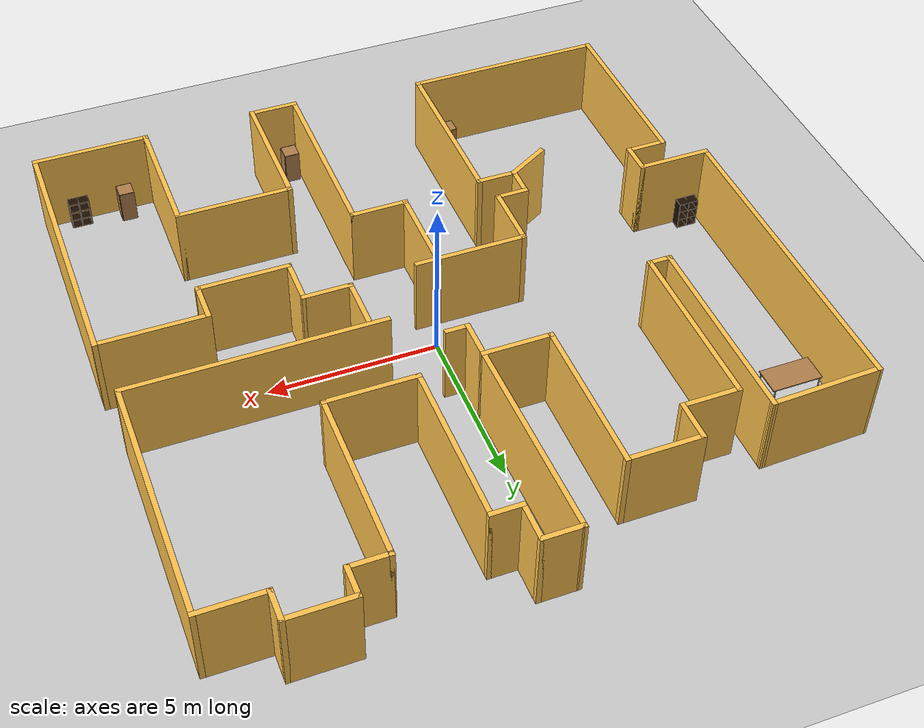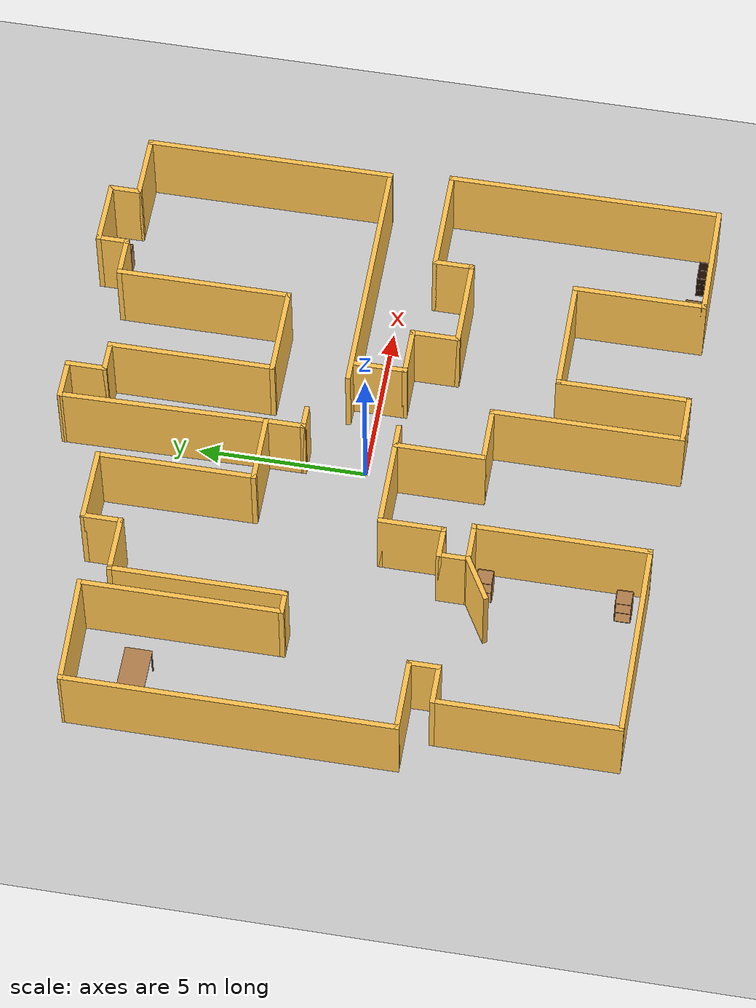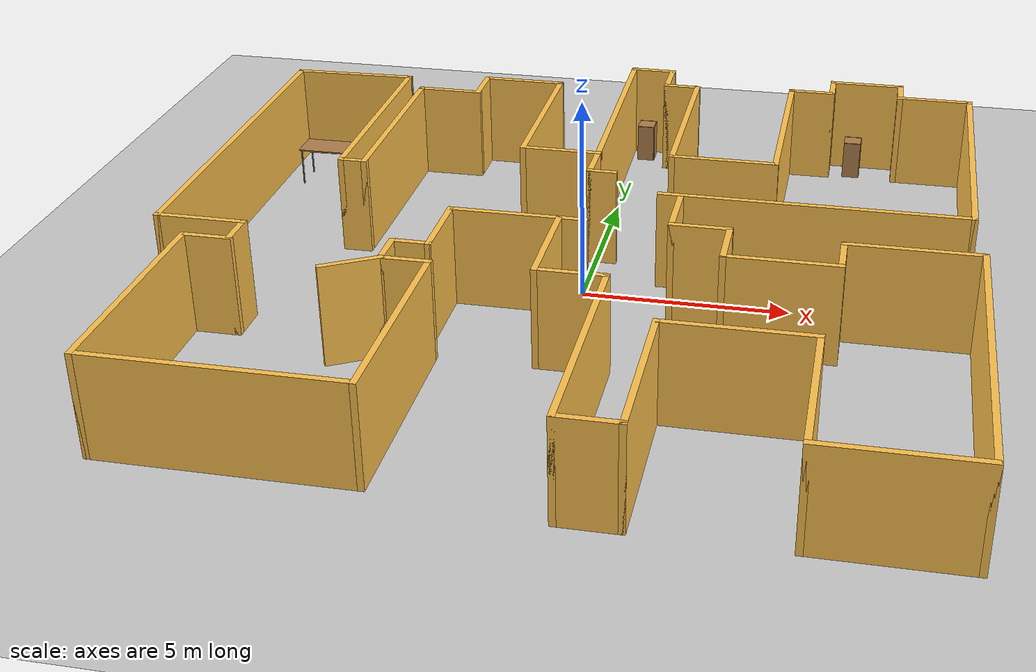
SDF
<sdf version="1.6">
 <world name="default">
  <light name="sun" type="directional">
   <pose>0 0 10 0 -0 0</pose>
   <diffuse>0.8 0.8 0.8 1</diffuse>
   <specular>0.2 0.2 0.2 1</specular>
   <attenuation>
    <range>1000</range>
    <constant>0.9</constant>
    <linear>0.01</linear>
    <quadratic>0.001</quadratic>
   </attenuation>
   <direction>-0.5 0.1 -0.9</direction>
  </light>
  <model name="ground_plane">
   <static>1</static>
   <link name="link">
    <collision name="collision">
     <geometry><plane><normal>0 0 1</normal><size>100 100</size></plane></geometry>
     <surface>
      <contact><collide_bitmask>65535</collide_bitmask></contact>
      <friction><ode><mu>100</mu><mu2>50</mu2></ode></friction>
     </surface>
    </collision>
    <visual name="visual">
     <cast_shadows>0</cast_shadows>
     <geometry><plane><normal>0 0 1</normal><size>100 100</size></plane></geometry>
     <material>
      <script><uri>file://media/materials/scripts/gazebo.material</uri><name>Gazebo/Grey</name></script>
     </material>
    </visual>
   </link>
  </model>
  <gravity>0 0 -9.8</gravity>
  <magnetic_field>6e-06 2.3e-05 -4.2e-05</magnetic_field>
  <atmosphere type="adiabatic"/>
  <physics name="default_physics" default="0" type="ode">
   <max_step_size>0.001</max_step_size>
   <real_time_factor>1</real_time_factor>
   <real_time_update_rate>1000</real_time_update_rate>
  </physics>
  <scene><ambient>0.4 0.4 0.4 1</ambient><background>0.7 0.7 0.7 1</background><shadows>1</shadows></scene>
  <audio><device>default</device></audio>
  <spherical_coordinates>
   <surface_model>EARTH_WGS84</surface_model>
   <latitude_deg>0</latitude_deg>
   <longitude_deg>0</longitude_deg>
   <elevation>0</elevation>
   <heading_deg>0</heading_deg>
  </spherical_coordinates>
  <model name="map_118">
   <pose>-0.142364 -0.062116 0 0 -0 0</pose>
   <link name="Wall_10">
    <collision name="Wall_10_Collision">
     <geometry><box><size>5.25 0.15 2.5</size></box></geometry>
     <pose>0 0 1.25 0 -0 0</pose>
    </collision>
    <visual name="Wall_10_Visual">
     <pose>0 0 1.25 0 -0 0</pose>
     <geometry><box><size>5.25 0.15 2.5</size></box></geometry>
     <material>
      <script><uri>file://media/materials/scripts/gazebo.material</uri><name>Gazebo/Grey</name></script>
      <ambient>1 0.764706 0.305882 1</ambient>
     </material>
     <meta><layer>0</layer></meta>
    </visual>
    <pose>-2.57383 -6.12539 0 0 -0 1.5708</pose>
   </link>
   <link name="Wall_11">
    <collision name="Wall_11_Collision">
     <geometry><box><size>1.25 0.15 2.5</size></box></geometry>
     <pose>0 0 1.25 0 -0 0</pose>
    </collision>
    <visual name="Wall_11_Visual">
     <pose>0 0 1.25 0 -0 0</pose>
     <geometry><box><size>1.25 0.15 2.5</size></box></geometry>
     <material>
      <script><uri>file://media/materials/scripts/gazebo.material</uri><name>Gazebo/Grey</name></script>
      <ambient>1 0.764706 0.305882 1</ambient>
     </material>
     <meta><layer>0</layer></meta>
    </visual>
    <pose>-3.12383 -3.57539 0 0 -0 3.14159</pose>
   </link>
   <link name="Wall_12">
    <collision name="Wall_12_Collision">
     <geometry><box><size>1 0.15 2.5</size></box></geometry>
     <pose>0 0 1.25 0 -0 0</pose>
    </collision>
    <visual name="Wall_12_Visual">
     <pose>0 0 1.25 0 -0 0</pose>
     <geometry><box><size>1 0.15 2.5</size></box></geometry>
     <material>
      <script><uri>file://media/materials/scripts/gazebo.material</uri><name>Gazebo/Grey</name></script>
      <ambient>1 0.764706 0.305882 1</ambient>
     </material>
     <meta><layer>0</layer></meta>
    </visual>
    <pose>-3.67383 -3.15039 0 0 -0 1.5708</pose>
   </link>
   <link name="Wall_13">
    <collision name="Wall_13_Collision">
     <geometry><box><size>1 0.15 2.5</size></box></geometry>
     <pose>0 0 1.25 0 -0 0</pose>
    </collision>
    <visual name="Wall_13_Visual">
     <pose>0 0 1.25 0 -0 0</pose>
     <geometry><box><size>1 0.15 2.5</size></box></geometry>
     <material>
      <script><uri>file://media/materials/scripts/gazebo.material</uri><name>Gazebo/Grey</name></script>
      <ambient>1 0.764706 0.305882 1</ambient>
     </material>
     <meta><layer>0</layer></meta>
    </visual>
    <pose>-3.24883 -2.72539 0 0 -0 0</pose>
   </link>
   <link name="Wall_14">
    <collision name="Wall_14_Collision">
     <geometry><box><size>2 0.15 2.5</size></box></geometry>
     <pose>0 0 1.25 0 -0 0</pose>
    </collision>
    <visual name="Wall_14_Visual">
     <pose>0 0 1.25 0 -0 0</pose>
     <geometry><box><size>2 0.15 2.5</size></box></geometry>
     <material>
      <script><uri>file://media/materials/scripts/gazebo.material</uri><name>Gazebo/Grey</name></script>
      <ambient>1 0.764706 0.305882 1</ambient>
     </material>
     <meta><layer>0</layer></meta>
    </visual>
    <pose>-2.82383 -1.80039 0 0 -0 1.5708</pose>
   </link>
   <link name="Wall_15">
    <collision name="Wall_15_Collision">
     <geometry><box><size>2.75 0.15 2.5</size></box></geometry>
     <pose>0 0 1.25 0 -0 0</pose>
    </collision>
    <visual name="Wall_15_Visual">
     <pose>0 0 1.25 0 -0 0</pose>
     <geometry><box><size>2.75 0.15 2.5</size></box></geometry>
     <material>
      <script><uri>file://media/materials/scripts/gazebo.material</uri><name>Gazebo/Grey</name></script>
      <ambient>1 0.764706 0.305882 1</ambient>
     </material>
     <meta><layer>0</layer></meta>
    </visual>
    <pose>-1.52383 -0.87539 0 0 -0 0</pose>
   </link>
   <link name="Wall_16">
    <collision name="Wall_16_Collision">
     <geometry><box><size>2.75 0.15 2.5</size></box></geometry>
     <pose>0 0 1.25 0 -0 0</pose>
    </collision>
    <visual name="Wall_16_Visual">
     <pose>0 0 1.25 0 -0 0</pose>
     <geometry><box><size>2.75 0.15 2.5</size></box></geometry>
     <material>
      <script><uri>file://media/materials/scripts/gazebo.material</uri><name>Gazebo/Grey</name></script>
      <ambient>1 0.764706 0.305882 1</ambient>
     </material>
     <meta><layer>0</layer></meta>
    </visual>
    <pose>-0.223829 -2.17539 0 0 -0 -1.5708</pose>
   </link>
   <link name="Wall_17">
    <collision name="Wall_17_Collision">
     <geometry><box><size>1.75 0.15 2.5</size></box></geometry>
     <pose>0 0 1.25 0 -0 0</pose>
    </collision>
    <visual name="Wall_17_Visual">
     <pose>0 0 1.25 0 -0 0</pose>
     <geometry><box><size>1.75 0.15 2.5</size></box></geometry>
     <material>
      <script><uri>file://media/materials/scripts/gazebo.material</uri><name>Gazebo/Grey</name></script>
      <ambient>1 0.764706 0.305882 1</ambient>
     </material>
     <meta><layer>0</layer></meta>
    </visual>
    <pose>0.576171 -3.47539 0 0 -0 0</pose>
   </link>
   <link name="Wall_18">
    <collision name="Wall_18_Collision">
     <geometry><box><size>5.75 0.15 2.5</size></box></geometry>
     <pose>0 0 1.25 0 -0 0</pose>
    </collision>
    <visual name="Wall_18_Visual">
     <pose>0 0 1.25 0 -0 0</pose>
     <geometry><box><size>5.75 0.15 2.5</size></box></geometry>
     <material>
      <script><uri>file://media/materials/scripts/gazebo.material</uri><name>Gazebo/Grey</name></script>
      <ambient>1 0.764706 0.305882 1</ambient>
     </material>
     <meta><layer>0</layer></meta>
    </visual>
    <pose>1.37617 -6.27539 0 0 -0 -1.5708</pose>
   </link>
   <link name="Wall_19">
    <collision name="Wall_19_Collision">
     <geometry><box><size>1.5 0.15 2.5</size></box></geometry>
     <pose>0 0 1.25 0 -0 0</pose>
    </collision>
    <visual name="Wall_19_Visual">
     <pose>0 0 1.25 0 -0 0</pose>
     <geometry><box><size>1.5 0.15 2.5</size></box></geometry>
     <material>
      <script><uri>file://media/materials/scripts/gazebo.material</uri><name>Gazebo/Grey</name></script>
      <ambient>1 0.764706 0.305882 1</ambient>
     </material>
     <meta><layer>0</layer></meta>
    </visual>
    <pose>2.05117 -9.07539 0 0 -0 0</pose>
   </link>
   <link name="Wall_20">
    <collision name="Wall_20_Collision">
     <geometry><box><size>4 0.15 2.5</size></box></geometry>
     <pose>0 0 1.25 0 -0 0</pose>
    </collision>
    <visual name="Wall_20_Visual">
     <pose>0 0 1.25 0 -0 0</pose>
     <geometry><box><size>4 0.15 2.5</size></box></geometry>
     <material>
      <script><uri>file://media/materials/scripts/gazebo.material</uri><name>Gazebo/Grey</name></script>
      <ambient>1 0.764706 0.305882 1</ambient>
     </material>
     <meta><layer>0</layer></meta>
    </visual>
    <pose>2.72617 -7.15039 0 0 -0 1.5708</pose>
   </link>
   <link name="Wall_21">
    <collision name="Wall_21_Collision">
     <geometry><box><size>3.5 0.15 2.5</size></box></geometry>
     <pose>0 0 1.25 0 -0 0</pose>
    </collision>
    <visual name="Wall_21_Visual">
     <pose>0 0 1.25 0 -0 0</pose>
     <geometry><box><size>3.5 0.15 2.5</size></box></geometry>
     <material>
      <script><uri>file://media/materials/scripts/gazebo.material</uri><name>Gazebo/Grey</name></script>
      <ambient>1 0.764706 0.305882 1</ambient>
     </material>
     <meta><layer>0</layer></meta>
    </visual>
    <pose>4.40117 -5.22539 0 0 -0 0</pose>
   </link>
   <link name="Wall_22">
    <collision name="Wall_22_Collision">
     <geometry><box><size>4 0.15 2.5</size></box></geometry>
     <pose>0 0 1.25 0 -0 0</pose>
    </collision>
    <visual name="Wall_22_Visual">
     <pose>0 0 1.25 0 -0 0</pose>
     <geometry><box><size>4 0.15 2.5</size></box></geometry>
     <material>
      <script><uri>file://media/materials/scripts/gazebo.material</uri><name>Gazebo/Grey</name></script>
      <ambient>1 0.764706 0.305882 1</ambient>
     </material>
     <meta><layer>0</layer></meta>
    </visual>
    <pose>6.07617 -7.15039 0 0 -0 -1.5708</pose>
   </link>
   <link name="Wall_23">
    <collision name="Wall_23_Collision">
     <geometry><box><size>3.5 0.15 2.5</size></box></geometry>
     <pose>0 0 1.25 0 -0 0</pose>
    </collision>
    <visual name="Wall_23_Visual">
     <pose>0 0 1.25 0 -0 0</pose>
     <geometry><box><size>3.5 0.15 2.5</size></box></geometry>
     <material>
      <script><uri>file://media/materials/scripts/gazebo.material</uri><name>Gazebo/Grey</name></script>
      <ambient>1 0.764706 0.305882 1</ambient>
     </material>
     <meta><layer>0</layer></meta>
    </visual>
    <pose>7.75117 -9.07539 0 0 -0 0</pose>
   </link>
   <link name="Wall_24">
    <collision name="Wall_24_Collision">
     <geometry><box><size>8.25 0.15 2.5</size></box></geometry>
     <pose>0 0 1.25 0 -0 0</pose>
    </collision>
    <visual name="Wall_24_Visual">
     <pose>0 0 1.25 0 -0 0</pose>
     <geometry><box><size>8.25 0.15 2.5</size></box></geometry>
     <material>
      <script><uri>file://media/materials/scripts/gazebo.material</uri><name>Gazebo/Grey</name></script>
      <ambient>1 0.764706 0.305882 1</ambient>
     </material>
     <meta><layer>0</layer></meta>
    </visual>
    <pose>9.42617 -5.02539 0 0 -0 1.5708</pose>
   </link>
   <link name="Wall_25">
    <collision name="Wall_25_Collision">
     <geometry><box><size>3.25 0.15 2.5</size></box></geometry>
     <pose>0 0 1.25 0 -0 0</pose>
    </collision>
    <visual name="Wall_25_Visual">
     <pose>0 0 1.25 0 -0 0</pose>
     <geometry><box><size>3.25 0.15 2.5</size></box></geometry>
     <material>
      <script><uri>file://media/materials/scripts/gazebo.material</uri><name>Gazebo/Grey</name></script>
      <ambient>1 0.764706 0.305882 1</ambient>
     </material>
     <meta><layer>0</layer></meta>
    </visual>
    <pose>7.87617 -0.97539 0 0 -0 3.14159</pose>
   </link>
   <link name="Wall_26">
    <collision name="Wall_26_Collision">
     <geometry><box><size>1.25 0.15 2.5</size></box></geometry>
     <pose>0 0 1.25 0 -0 0</pose>
    </collision>
    <visual name="Wall_26_Visual">
     <pose>0 0 1.25 0 -0 0</pose>
     <geometry><box><size>1.25 0.15 2.5</size></box></geometry>
     <material>
      <script><uri>file://media/materials/scripts/gazebo.material</uri><name>Gazebo/Grey</name></script>
      <ambient>1 0.764706 0.305882 1</ambient>
     </material>
     <meta><layer>0</layer></meta>
    </visual>
    <pose>6.32617 -1.52539 0 0 -0 -1.5708</pose>
   </link>
   <link name="Wall_27">
    <collision name="Wall_27_Collision">
     <geometry><box><size>2.75 0.15 2.5</size></box></geometry>
     <pose>0 0 1.25 0 -0 0</pose>
    </collision>
    <visual name="Wall_27_Visual">
     <pose>0 0 1.25 0 -0 0</pose>
     <geometry><box><size>2.75 0.15 2.5</size></box></geometry>
     <material>
      <script><uri>file://media/materials/scripts/gazebo.material</uri><name>Gazebo/Grey</name></script>
      <ambient>1 0.764706 0.305882 1</ambient>
     </material>
     <meta><layer>0</layer></meta>
    </visual>
    <pose>5.02617 -2.07539 0 0 -0 3.14159</pose>
   </link>
   <link name="Wall_28">
    <collision name="Wall_28_Collision">
     <geometry><box><size>1.5 0.15 2.5</size></box></geometry>
     <pose>0 0 1.25 0 -0 0</pose>
    </collision>
    <visual name="Wall_28_Visual">
     <pose>0 0 1.25 0 -0 0</pose>
     <geometry><box><size>1.5 0.15 2.5</size></box></geometry>
     <material>
      <script><uri>file://media/materials/scripts/gazebo.material</uri><name>Gazebo/Grey</name></script>
      <ambient>1 0.764706 0.305882 1</ambient>
     </material>
     <meta><layer>0</layer></meta>
    </visual>
    <pose>3.72617 -1.40039 0 0 -0 1.5708</pose>
   </link>
   <link name="Wall_33">
    <collision name="Wall_33_Collision">
     <geometry><box><size>2 0.15 2.5</size></box></geometry>
     <pose>0 0 1.25 0 -0 0</pose>
    </collision>
    <visual name="Wall_33_Visual">
     <pose>0 0 1.25 0 -0 0</pose>
     <geometry><box><size>2 0.15 2.5</size></box></geometry>
     <material>
      <script><uri>file://media/materials/scripts/gazebo.material</uri><name>Gazebo/Grey</name></script>
      <ambient>1 0.764706 0.305882 1</ambient>
     </material>
     <meta><layer>0</layer></meta>
    </visual>
    <pose>8.30117 8.22461 0 0 -0 3.14159</pose>
   </link>
   <link name="Wall_34">
    <collision name="Wall_34_Collision">
     <geometry><box><size>1 0.15 2.5</size></box></geometry>
     <pose>0 0 1.25 0 -0 0</pose>
    </collision>
    <visual name="Wall_34_Visual">
     <pose>0 0 1.25 0 -0 0</pose>
     <geometry><box><size>1 0.15 2.5</size></box></geometry>
     <material>
      <script><uri>file://media/materials/scripts/gazebo.material</uri><name>Gazebo/Grey</name></script>
      <ambient>1 0.764706 0.305882 1</ambient>
     </material>
     <meta><layer>0</layer></meta>
    </visual>
    <pose>7.37617 8.64961 0 0 -0 1.5708</pose>
   </link>
   <link name="Wall_35">
    <collision name="Wall_35_Collision">
     <geometry><box><size>2 0.15 2.5</size></box></geometry>
     <pose>0 0 1.25 0 -0 0</pose>
    </collision>
    <visual name="Wall_35_Visual">
     <pose>0 0 1.25 0 -0 0</pose>
     <geometry><box><size>2 0.15 2.5</size></box></geometry>
     <material>
      <script><uri>file://media/materials/scripts/gazebo.material</uri><name>Gazebo/Grey</name></script>
      <ambient>1 0.764706 0.305882 1</ambient>
     </material>
     <meta><layer>0</layer></meta>
    </visual>
    <pose>6.45117 9.07461 0 0 -0 3.14159</pose>
   </link>
   <link name="Wall_36">
    <collision name="Wall_36_Collision">
     <geometry><box><size>1 0.15 2.5</size></box></geometry>
     <pose>0 0 1.25 0 -0 0</pose>
    </collision>
    <visual name="Wall_36_Visual">
     <pose>0 0 1.25 0 -0 0</pose>
     <geometry><box><size>1 0.15 2.5</size></box></geometry>
     <material>
      <script><uri>file://media/materials/scripts/gazebo.material</uri><name>Gazebo/Grey</name></script>
      <ambient>1 0.764706 0.305882 1</ambient>
     </material>
     <meta><layer>0</layer></meta>
    </visual>
    <pose>5.52617 8.64961 0 0 -0 -1.5708</pose>
   </link>
   <link name="Wall_37">
    <collision name="Wall_37_Collision">
     <geometry><box><size>1.25 0.15 2.5</size></box></geometry>
     <pose>0 0 1.25 0 -0 0</pose>
    </collision>
    <visual name="Wall_37_Visual">
     <pose>0 0 1.25 0 -0 0</pose>
     <geometry><box><size>1.25 0.15 2.5</size></box></geometry>
     <material>
      <script><uri>file://media/materials/scripts/gazebo.material</uri><name>Gazebo/Grey</name></script>
      <ambient>1 0.764706 0.305882 1</ambient>
     </material>
     <meta><layer>0</layer></meta>
    </visual>
    <pose>4.97617 8.22461 0 0 -0 3.14159</pose>
   </link>
   <link name="Wall_38">
    <collision name="Wall_38_Collision">
     <geometry><box><size>5.25 0.15 2.5</size></box></geometry>
     <pose>0 0 1.25 0 -0 0</pose>
    </collision>
    <visual name="Wall_38_Visual">
     <pose>0 0 1.25 0 -0 0</pose>
     <geometry><box><size>5.25 0.15 2.5</size></box></geometry>
     <material>
      <script><uri>file://media/materials/scripts/gazebo.material</uri><name>Gazebo/Grey</name></script>
      <ambient>1 0.764706 0.305882 1</ambient>
     </material>
     <meta><layer>0</layer></meta>
    </visual>
    <pose>4.42617 5.67461 0 0 -0 -1.5708</pose>
   </link>
   <link name="Wall_39">
    <collision name="Wall_39_Collision">
     <geometry><box><size>2.75 0.15 2.5</size></box></geometry>
     <pose>0 0 1.25 0 -0 0</pose>
    </collision>
    <visual name="Wall_39_Visual">
     <pose>0 0 1.25 0 -0 0</pose>
     <geometry><box><size>2.75 0.15 2.5</size></box></geometry>
     <material>
      <script><uri>file://media/materials/scripts/gazebo.material</uri><name>Gazebo/Grey</name></script>
      <ambient>1 0.764706 0.305882 1</ambient>
     </material>
     <meta><layer>0</layer></meta>
    </visual>
    <pose>3.12617 3.12461 0 0 -0 3.14159</pose>
   </link>
   <link name="Wall_4">
    <collision name="Wall_4_Collision">
     <geometry><box><size>9.75 0.15 2.5</size></box></geometry>
     <pose>0 0 1.25 0 -0 0</pose>
    </collision>
    <visual name="Wall_4_Visual">
     <pose>0 0 1.25 0 -0 0</pose>
     <geometry><box><size>9.75 0.15 2.5</size></box></geometry>
     <material>
      <script><uri>file://media/materials/scripts/gazebo.material</uri><name>Gazebo/Grey</name></script>
      <ambient>1 0.764706 0.305882 1</ambient>
     </material>
     <meta><layer>0</layer></meta>
    </visual>
    <pose>-9.42383 2.32461 0 0 -0 -1.5708</pose>
   </link>
   <link name="Wall_40">
    <collision name="Wall_40_Collision">
     <geometry><box><size>5 0.15 2.5</size></box></geometry>
     <pose>0 0 1.25 0 -0 0</pose>
    </collision>
    <visual name="Wall_40_Visual">
     <pose>0 0 1.25 0 -0 0</pose>
     <geometry><box><size>5 0.15 2.5</size></box></geometry>
     <material>
      <script><uri>file://media/materials/scripts/gazebo.material</uri><name>Gazebo/Grey</name></script>
      <ambient>1 0.764706 0.305882 1</ambient>
     </material>
     <meta><layer>0</layer></meta>
    </visual>
    <pose>1.82617 5.54961 0 0 -0 1.5708</pose>
   </link>
   <link name="Wall_43">
    <collision name="Wall_43_Collision">
     <geometry><box><size>1 0.15 2.5</size></box></geometry>
     <pose>0 0 1.25 0 -0 0</pose>
    </collision>
    <visual name="Wall_43_Visual">
     <pose>0 0 1.25 0 -0 0</pose>
     <geometry><box><size>1 0.15 2.5</size></box></geometry>
     <material>
      <script><uri>file://media/materials/scripts/gazebo.material</uri><name>Gazebo/Grey</name></script>
      <ambient>1 0.764706 0.305882 1</ambient>
     </material>
     <meta><layer>0</layer></meta>
    </visual>
    <pose>1.40117 7.97461 0 0 -0 3.14159</pose>
   </link>
   <link name="Wall_44">
    <collision name="Wall_44_Collision">
     <geometry><box><size>1.25 0.15 2.5</size></box></geometry>
     <pose>0 0 1.25 0 -0 0</pose>
    </collision>
    <visual name="Wall_44_Visual">
     <pose>0 0 1.25 0 -0 0</pose>
     <geometry><box><size>1.25 0.15 2.5</size></box></geometry>
     <material>
      <script><uri>file://media/materials/scripts/gazebo.material</uri><name>Gazebo/Grey</name></script>
      <ambient>1 0.764706 0.305882 1</ambient>
     </material>
     <meta><layer>0</layer></meta>
    </visual>
    <pose>0.976171 8.52461 0 0 -0 1.5708</pose>
   </link>
   <link name="Wall_45">
    <collision name="Wall_45_Collision">
     <geometry><box><size>1.25 0.15 2.5</size></box></geometry>
     <pose>0 0 1.25 0 -0 0</pose>
    </collision>
    <visual name="Wall_45_Visual">
     <pose>0 0 1.25 0 -0 0</pose>
     <geometry><box><size>1.25 0.15 2.5</size></box></geometry>
     <material>
      <script><uri>file://media/materials/scripts/gazebo.material</uri><name>Gazebo/Grey</name></script>
      <ambient>1 0.764706 0.305882 1</ambient>
     </material>
     <meta><layer>0</layer></meta>
    </visual>
    <pose>0.426171 9.07461 0 0 -0 3.14159</pose>
   </link>
   <link name="Wall_46">
    <collision name="Wall_46_Collision">
     <geometry><box><size>6.25 0.15 2.5</size></box></geometry>
     <pose>0 0 1.25 0 -0 0</pose>
    </collision>
    <visual name="Wall_46_Visual">
     <pose>0 0 1.25 0 -0 0</pose>
     <geometry><box><size>6.25 0.15 2.5</size></box></geometry>
     <material>
      <script><uri>file://media/materials/scripts/gazebo.material</uri><name>Gazebo/Grey</name></script>
      <ambient>1 0.764706 0.305882 1</ambient>
     </material>
     <meta><layer>0</layer></meta>
    </visual>
    <pose>-0.077305 6.02461 0 0 -0 -1.55554</pose>
   </link>
   <link name="Wall_47">
    <collision name="Wall_47_Collision">
     <geometry><box><size>2.09305 0.15 2.5</size></box></geometry>
     <pose>0 0 1.25 0 -0 0</pose>
    </collision>
    <visual name="Wall_47_Visual">
     <pose>0 0 1.25 0 -0 0</pose>
     <geometry><box><size>2.09305 0.15 2.5</size></box></geometry>
     <material>
      <script><uri>file://media/materials/scripts/gazebo.material</uri><name>Gazebo/Grey</name></script>
      <ambient>1 0.764706 0.305882 1</ambient>
     </material>
     <meta><layer>0</layer></meta>
    </visual>
    <pose>-1.00231 2.97461 0 0 -0 3.14159</pose>
   </link>
   <link name="Wall_48">
    <collision name="Wall_48_Collision">
     <geometry><box><size>4.75 0.15 2.5</size></box></geometry>
     <pose>0 0 1.25 0 -0 0</pose>
    </collision>
    <visual name="Wall_48_Visual">
     <pose>0 0 1.25 0 -0 0</pose>
     <geometry><box><size>4.75 0.15 2.5</size></box></geometry>
     <material>
      <script><uri>file://media/materials/scripts/gazebo.material</uri><name>Gazebo/Grey</name></script>
      <ambient>1 0.764706 0.305882 1</ambient>
     </material>
     <meta><layer>0</layer></meta>
    </visual>
    <pose>-1.97383 5.27461 0 0 -0 1.5708</pose>
   </link>
   <link name="Wall_49">
    <collision name="Wall_49_Collision">
     <geometry><box><size>2.25 0.15 2.5</size></box></geometry>
     <pose>0 0 1.25 0 -0 0</pose>
    </collision>
    <visual name="Wall_49_Visual">
     <pose>0 0 1.25 0 -0 0</pose>
     <geometry><box><size>2.25 0.15 2.5</size></box></geometry>
     <material>
      <script><uri>file://media/materials/scripts/gazebo.material</uri><name>Gazebo/Grey</name></script>
      <ambient>1 0.764706 0.305882 1</ambient>
     </material>
     <meta><layer>0</layer></meta>
    </visual>
    <pose>-3.02383 7.57461 0 0 -0 3.14159</pose>
   </link>
   <link name="Wall_5">
    <collision name="Wall_5_Collision">
     <geometry><box><size>2.25 0.15 2.5</size></box></geometry>
     <pose>0 0 1.25 0 -0 0</pose>
    </collision>
    <visual name="Wall_5_Visual">
     <pose>0 0 1.25 0 -0 0</pose>
     <geometry><box><size>2.25 0.15 2.5</size></box></geometry>
     <material>
      <script><uri>file://media/materials/scripts/gazebo.material</uri><name>Gazebo/Grey</name></script>
      <ambient>1 0.764706 0.305882 1</ambient>
     </material>
     <meta><layer>0</layer></meta>
    </visual>
    <pose>-8.37383 -2.47539 0 0 -0 0</pose>
   </link>
   <link name="Wall_50">
    <collision name="Wall_50_Collision">
     <geometry><box><size>1.25 0.15 2.5</size></box></geometry>
     <pose>0 0 1.25 0 -0 0</pose>
    </collision>
    <visual name="Wall_50_Visual">
     <pose>0 0 1.25 0 -0 0</pose>
     <geometry><box><size>1.25 0.15 2.5</size></box></geometry>
     <material>
      <script><uri>file://media/materials/scripts/gazebo.material</uri><name>Gazebo/Grey</name></script>
      <ambient>1 0.764706 0.305882 1</ambient>
     </material>
     <meta><layer>0</layer></meta>
    </visual>
    <pose>-4.07383 7.02461 0 0 -0 -1.5708</pose>
   </link>
   <link name="Wall_51">
    <collision name="Wall_51_Collision">
     <geometry><box><size>1.75 0.15 2.5</size></box></geometry>
     <pose>0 0 1.25 0 -0 0</pose>
    </collision>
    <visual name="Wall_51_Visual">
     <pose>0 0 1.25 0 -0 0</pose>
     <geometry><box><size>1.75 0.15 2.5</size></box></geometry>
     <material>
      <script><uri>file://media/materials/scripts/gazebo.material</uri><name>Gazebo/Grey</name></script>
      <ambient>1 0.764706 0.305882 1</ambient>
     </material>
     <meta><layer>0</layer></meta>
    </visual>
    <pose>-4.87383 6.47461 0 0 -0 3.14159</pose>
   </link>
   <link name="Wall_52">
    <collision name="Wall_52_Collision">
     <geometry><box><size>5.25 0.15 2.5</size></box></geometry>
     <pose>0 0 1.25 0 -0 0</pose>
    </collision>
    <visual name="Wall_52_Visual">
     <pose>0 0 1.25 0 -0 0</pose>
     <geometry><box><size>5.25 0.15 2.5</size></box></geometry>
     <material>
      <script><uri>file://media/materials/scripts/gazebo.material</uri><name>Gazebo/Grey</name></script>
      <ambient>1 0.764706 0.305882 1</ambient>
     </material>
     <meta><layer>0</layer></meta>
    </visual>
    <pose>-5.67383 3.92461 0 0 -0 -1.5708</pose>
   </link>
   <link name="Wall_53">
    <collision name="Wall_53_Collision">
     <geometry><box><size>0.75 0.15 2.5</size></box></geometry>
     <pose>0 0 1.25 0 -0 0</pose>
    </collision>
    <visual name="Wall_53_Visual">
     <pose>0 0 1.25 0 -0 0</pose>
     <geometry><box><size>0.75 0.15 2.5</size></box></geometry>
     <material>
      <script><uri>file://media/materials/scripts/gazebo.material</uri><name>Gazebo/Grey</name></script>
      <ambient>1 0.764706 0.305882 1</ambient>
     </material>
     <meta><layer>0</layer></meta>
    </visual>
    <pose>-5.97383 1.37461 0 0 -0 3.14159</pose>
   </link>
   <link name="Wall_54">
    <collision name="Wall_54_Collision">
     <geometry><box><size>6 0.15 2.5</size></box></geometry>
     <pose>0 0 1.25 0 -0 0</pose>
    </collision>
    <visual name="Wall_54_Visual">
     <pose>0 0 1.25 0 -0 0</pose>
     <geometry><box><size>6 0.15 2.5</size></box></geometry>
     <material>
      <script><uri>file://media/materials/scripts/gazebo.material</uri><name>Gazebo/Grey</name></script>
      <ambient>1 0.764706 0.305882 1</ambient>
     </material>
     <meta><layer>0</layer></meta>
    </visual>
    <pose>-6.27383 4.29961 0 0 -0 1.5708</pose>
   </link>
   <link name="Wall_55">
    <collision name="Wall_55_Collision">
     <geometry><box><size>3.30159 0.15 2.5</size></box></geometry>
     <pose>0 0 1.25 0 -0 0</pose>
    </collision>
    <visual name="Wall_55_Visual">
     <pose>0 0 1.25 0 -0 0</pose>
     <geometry><box><size>3.30159 0.15 2.5</size></box></geometry>
     <material>
      <script><uri>file://media/materials/scripts/gazebo.material</uri><name>Gazebo/Grey</name></script>
      <ambient>1 0.764706 0.305882 1</ambient>
     </material>
     <meta><layer>0</layer></meta>
    </visual>
    <pose>-7.84883 7.17461 0 0 -0 -3.10986</pose>
   </link>
   <link name="Wall_57">
    <collision name="Wall_57_Collision">
     <geometry><box><size>1.5 0.15 2.5</size></box></geometry>
     <pose>0 0 1.25 0 -0 0</pose>
    </collision>
    <visual name="Wall_57_Visual">
     <pose>0 0 1.25 0 -0 0</pose>
     <geometry><box><size>1.5 0.15 2.5</size></box></geometry>
     <material>
      <script><uri>file://media/materials/scripts/gazebo.material</uri><name>Gazebo/Grey</name></script>
      <ambient>1 0.764706 0.305882 1</ambient>
     </material>
     <meta><layer>0</layer></meta>
    </visual>
    <pose>-4.2584 -3.91289 0 0 -0 -2.61799</pose>
   </link>
   <link name="Wall_6">
    <collision name="Wall_6_Collision">
     <geometry><box><size>1 0.15 2.5</size></box></geometry>
     <pose>0 0 1.25 0 -0 0</pose>
    </collision>
    <visual name="Wall_6_Visual">
     <pose>0 0 1.25 0 -0 0</pose>
     <geometry><box><size>1 0.15 2.5</size></box></geometry>
     <material>
      <script><uri>file://media/materials/scripts/gazebo.material</uri><name>Gazebo/Grey</name></script>
      <ambient>1 0.764706 0.305882 1</ambient>
     </material>
     <meta><layer>0</layer></meta>
    </visual>
    <pose>-7.32383 -2.90039 0 0 -0 -1.5708</pose>
   </link>
   <link name="Wall_63">
    <collision name="Wall_63_Collision">
     <geometry><box><size>1.25 0.15 2.5</size></box></geometry>
     <pose>0 0 1.25 0 -0 0</pose>
    </collision>
    <visual name="Wall_63_Visual">
     <pose>0 0 1.25 0 -0 0</pose>
     <geometry><box><size>1.25 0.15 2.5</size></box></geometry>
     <material>
      <script><uri>file://media/materials/scripts/gazebo.material</uri><name>Gazebo/Grey</name></script>
      <ambient>1 0.764706 0.305882 1</ambient>
     </material>
     <meta><layer>0</layer></meta>
    </visual>
    <pose>-0.030782 2.42461 0 0 -0 -1.5708</pose>
   </link>
   <link name="Wall_65">
    <collision name="Wall_65_Collision">
     <geometry><box><size>0.75 0.15 2.5</size></box></geometry>
     <pose>0 0 1.25 0 -0 0</pose>
    </collision>
    <visual name="Wall_65_Visual">
     <pose>0 0 1.25 0 -0 0</pose>
     <geometry><box><size>0.75 0.15 2.5</size></box></geometry>
     <material>
      <script><uri>file://media/materials/scripts/gazebo.material</uri><name>Gazebo/Grey</name></script>
      <ambient>1 0.764706 0.305882 1</ambient>
     </material>
     <meta><layer>0</layer></meta>
    </visual>
    <pose>0.269218 1.87461 0 0 -0 0</pose>
   </link>
   <link name="Wall_69">
    <collision name="Wall_69_Collision">
     <geometry><box><size>7.5 0.15 2.5</size></box></geometry>
     <pose>0 0 1.25 0 -0 0</pose>
    </collision>
    <visual name="Wall_69_Visual">
     <pose>0 0 1.25 0 -0 0</pose>
     <geometry><box><size>7.5 0.15 2.5</size></box></geometry>
     <material>
      <script><uri>file://media/materials/scripts/gazebo.material</uri><name>Gazebo/Grey</name></script>
      <ambient>1 0.764706 0.305882 1</ambient>
     </material>
     <meta><layer>0</layer></meta>
    </visual>
    <pose>5.55117 0.87461 0 0 -0 0</pose>
   </link>
   <link name="Wall_7">
    <collision name="Wall_7_Collision">
     <geometry><box><size>1.25 0.15 2.5</size></box></geometry>
     <pose>0 0 1.25 0 -0 0</pose>
    </collision>
    <visual name="Wall_7_Visual">
     <pose>0 0 1.25 0 -0 0</pose>
     <geometry><box><size>1.25 0.15 2.5</size></box></geometry>
     <material>
      <script><uri>file://media/materials/scripts/gazebo.material</uri><name>Gazebo/Grey</name></script>
      <ambient>1 0.764706 0.305882 1</ambient>
     </material>
     <meta><layer>0</layer></meta>
    </visual>
    <pose>-7.87383 -3.32539 0 0 -0 3.14159</pose>
   </link>
   <link name="Wall_71">
    <collision name="Wall_71_Collision">
     <geometry><box><size>7.5 0.15 2.5</size></box></geometry>
     <pose>0 0 1.25 0 -0 0</pose>
    </collision>
    <visual name="Wall_71_Visual">
     <pose>0 0 1.25 0 -0 0</pose>
     <geometry><box><size>7.5 0.15 2.5</size></box></geometry>
     <material>
      <script><uri>file://media/materials/scripts/gazebo.material</uri><name>Gazebo/Grey</name></script>
      <ambient>1 0.764706 0.305882 1</ambient>
     </material>
     <meta><layer>0</layer></meta>
    </visual>
    <pose>9.22617 4.54961 0 0 -0 -1.5708</pose>
   </link>
   <link name="Wall_74">
    <collision name="Wall_74_Collision">
     <geometry><box><size>0.75 0.15 2.5</size></box></geometry>
     <pose>0 0 1.25 0 -0 0</pose>
    </collision>
    <visual name="Wall_74_Visual">
     <pose>0 0 1.25 0 -0 0</pose>
     <geometry><box><size>0.75 0.15 2.5</size></box></geometry>
     <material>
      <script><uri>file://media/materials/scripts/gazebo.material</uri><name>Gazebo/Grey</name></script>
      <ambient>1 0.764706 0.305882 1</ambient>
     </material>
     <meta><layer>0</layer></meta>
    </visual>
    <pose>0.076171 -0.87539 0 0 -0 0</pose>
   </link>
   <link name="Wall_76">
    <collision name="Wall_76_Collision">
     <geometry><box><size>1.5 0.15 2.5</size></box></geometry>
     <pose>0 0 1.25 0 -0 0</pose>
    </collision>
    <visual name="Wall_76_Visual">
     <pose>0 0 1.25 0 -0 0</pose>
     <geometry><box><size>1.5 0.15 2.5</size></box></geometry>
     <material>
      <script><uri>file://media/materials/scripts/gazebo.material</uri><name>Gazebo/Grey</name></script>
      <ambient>1 0.764706 0.305882 1</ambient>
     </material>
     <meta><layer>0</layer></meta>
    </visual>
    <pose>3.05117 -0.72539 0 0 -0 3.14159</pose>
   </link>
   <link name="Wall_77">
    <collision name="Wall_77_Collision">
     <geometry><box><size>1.75 0.15 2.5</size></box></geometry>
     <pose>0 0 1.25 0 -0 0</pose>
    </collision>
    <visual name="Wall_77_Visual">
     <pose>0 0 1.25 0 -0 0</pose>
     <geometry><box><size>1.75 0.15 2.5</size></box></geometry>
     <material>
      <script><uri>file://media/materials/scripts/gazebo.material</uri><name>Gazebo/Grey</name></script>
      <ambient>1 0.764706 0.305882 1</ambient>
     </material>
     <meta><layer>0</layer></meta>
    </visual>
    <pose>2.37617 0.07461 0 0 -0 1.5708</pose>
   </link>
   <link name="Wall_8">
    <collision name="Wall_8_Collision">
     <geometry><box><size>5.5 0.15 2.5</size></box></geometry>
     <pose>0 0 1.25 0 -0 0</pose>
    </collision>
    <visual name="Wall_8_Visual">
     <pose>0 0 1.25 0 -0 0</pose>
     <geometry><box><size>5.5 0.15 2.5</size></box></geometry>
     <material>
      <script><uri>file://media/materials/scripts/gazebo.material</uri><name>Gazebo/Grey</name></script>
      <ambient>1 0.764706 0.305882 1</ambient>
     </material>
     <meta><layer>0</layer></meta>
    </visual>
    <pose>-8.42383 -6.00039 0 0 -0 -1.5708</pose>
   </link>
   <link name="Wall_9">
    <collision name="Wall_9_Collision">
     <geometry><box><size>6 0.15 2.5</size></box></geometry>
     <pose>0 0 1.25 0 -0 0</pose>
    </collision>
    <visual name="Wall_9_Visual">
     <pose>0 0 1.25 0 -0 0</pose>
     <geometry><box><size>6 0.15 2.5</size></box></geometry>
     <material>
      <script><uri>file://media/materials/scripts/gazebo.material</uri><name>Gazebo/Grey</name></script>
      <ambient>1 0.764706 0.305882 1</ambient>
     </material>
     <meta><layer>0</layer></meta>
    </visual>
    <pose>-5.49883 -8.67539 0 0 -0 0</pose>
   </link>
   <static>1</static>
  </model>
  <model name="cabinet">
   <static>1</static>
   <link name="cabinet_bottom_plate">
    <inertial>
     <pose>0 0 -1 0 -0 0</pose>
     <inertia><ixx>2.05</ixx><ixy>0</ixy><ixz>0</ixz><iyy>2.05</iyy><iyz>0</iyz><izz>2.05</izz></inertia>
     <mass>25</mass>
    </inertial>
    <collision name="cabinet_bottom_plate_geom">
     <pose>0 0 0.01 0 -0 0</pose>
     <geometry><box><size>0.45 0.45 0.02</size></box></geometry>
    </collision>
    <visual name="cabinet_bottom_plate_geom_visual">
     <pose>0 0 0.01 0 -0 0</pose>
     <geometry><box><size>0.45 0.45 0.02</size></box></geometry>
     <material>
      <script><uri>file://media/materials/scripts/gazebo.material</uri><name>Gazebo/Wood</name></script>
     </material>
    </visual>
    <collision name="cabinet_bottom_plate_geom_cabinet_back_plate">
     <pose>0.235 0 0.51 0 -0 0</pose>
     <geometry><box><size>0.02 0.45 1.02</size></box></geometry>
    </collision>
    <visual name="cabinet_bottom_plate_geom_cabinet_back_plate_visual">
     <pose>0.235 0 0.51 0 -0 0</pose>
     <geometry><box><size>0.02 0.45 1.02</size></box></geometry>
     <material>
      <script><uri>file://media/materials/scripts/gazebo.material</uri><name>Gazebo/Wood</name></script>
     </material>
    </visual>
    <collision name="cabinet_bottom_plate_geom_cabinet_left_plate">
     <pose>0 0.235 0.51 0 -0 0</pose>
     <geometry><box><size>0.45 0.02 1.02</size></box></geometry>
    </collision>
    <visual name="cabinet_bottom_plate_geom_cabinet_left_plate_visual">
     <pose>0 0.235 0.51 0 -0 0</pose>
     <geometry><box><size>0.45 0.02 1.02</size></box></geometry>
     <material>
      <script><uri>file://media/materials/scripts/gazebo.material</uri><name>Gazebo/Wood</name></script>
     </material>
    </visual>
    <collision name="cabinet_bottom_plate_geom_cabinet_middle_plate">
     <pose>0 0 0.51 0 -0 0</pose>
     <geometry><box><size>0.45 0.45 0.02</size></box></geometry>
    </collision>
    <visual name="cabinet_bottom_plate_geom_cabinet_middle_plate_visual">
     <pose>0 0 0.51 0 -0 0</pose>
     <geometry><box><size>0.45 0.45 0.02</size></box></geometry>
     <material>
      <script><uri>file://media/materials/scripts/gazebo.material</uri><name>Gazebo/Wood</name></script>
     </material>
    </visual>
    <collision name="cabinet_bottom_plate_geom_cabinet_right_plate">
     <pose>0 -0.235 0.51 0 -0 0</pose>
     <geometry><box><size>0.45 0.02 1.02</size></box></geometry>
    </collision>
    <visual name="cabinet_bottom_plate_geom_cabinet_right_plate_visual">
     <pose>0 -0.235 0.51 0 -0 0</pose>
     <geometry><box><size>0.45 0.02 1.02</size></box></geometry>
     <material>
      <script><uri>file://media/materials/scripts/gazebo.material</uri><name>Gazebo/Wood</name></script>
     </material>
    </visual>
    <collision name="cabinet_bottom_plate_geom_cabinet_top_plate">
     <pose>0 0 1.01 0 -0 0</pose>
     <geometry><box><size>0.45 0.45 0.02</size></box></geometry>
    </collision>
    <visual name="cabinet_bottom_plate_geom_cabinet_top_plate_visual">
     <pose>0 0 1.01 0 -0 0</pose>
     <geometry><box><size>0.45 0.45 0.02</size></box></geometry>
     <material>
      <script><uri>file://media/materials/scripts/gazebo.material</uri><name>Gazebo/Wood</name></script>
     </material>
    </visual>
   </link>
   <pose>-3.48549 -8.15949 0 0 -0 0</pose>
  </model>
  <model name="cabinet_0">
   <static>1</static>
   <link name="cabinet_bottom_plate">
    <inertial>
     <pose>0 0 -1 0 -0 0</pose>
     <inertia><ixx>2.05</ixx><ixy>0</ixy><ixz>0</ixz><iyy>2.05</iyy><iyz>0</iyz><izz>2.05</izz></inertia>
     <mass>25</mass>
    </inertial>
    <collision name="cabinet_bottom_plate_geom">
     <pose>0 0 0.01 0 -0 0</pose>
     <geometry><box><size>0.45 0.45 0.02</size></box></geometry>
    </collision>
    <visual name="cabinet_bottom_plate_geom_visual">
     <pose>0 0 0.01 0 -0 0</pose>
     <geometry><box><size>0.45 0.45 0.02</size></box></geometry>
     <material>
      <script><uri>file://media/materials/scripts/gazebo.material</uri><name>Gazebo/Wood</name></script>
     </material>
    </visual>
    <collision name="cabinet_bottom_plate_geom_cabinet_back_plate">
     <pose>0.235 0 0.51 0 -0 0</pose>
     <geometry><box><size>0.02 0.45 1.02</size></box></geometry>
    </collision>
    <visual name="cabinet_bottom_plate_geom_cabinet_back_plate_visual">
     <pose>0.235 0 0.51 0 -0 0</pose>
     <geometry><box><size>0.02 0.45 1.02</size></box></geometry>
     <material>
      <script><uri>file://media/materials/scripts/gazebo.material</uri><name>Gazebo/Wood</name></script>
     </material>
    </visual>
    <collision name="cabinet_bottom_plate_geom_cabinet_left_plate">
     <pose>0 0.235 0.51 0 -0 0</pose>
     <geometry><box><size>0.45 0.02 1.02</size></box></geometry>
    </collision>
    <visual name="cabinet_bottom_plate_geom_cabinet_left_plate_visual">
     <pose>0 0.235 0.51 0 -0 0</pose>
     <geometry><box><size>0.45 0.02 1.02</size></box></geometry>
     <material>
      <script><uri>file://media/materials/scripts/gazebo.material</uri><name>Gazebo/Wood</name></script>
     </material>
    </visual>
    <collision name="cabinet_bottom_plate_geom_cabinet_middle_plate">
     <pose>0 0 0.51 0 -0 0</pose>
     <geometry><box><size>0.45 0.45 0.02</size></box></geometry>
    </collision>
    <visual name="cabinet_bottom_plate_geom_cabinet_middle_plate_visual">
     <pose>0 0 0.51 0 -0 0</pose>
     <geometry><box><size>0.45 0.45 0.02</size></box></geometry>
     <material>
      <script><uri>file://media/materials/scripts/gazebo.material</uri><name>Gazebo/Wood</name></script>
     </material>
    </visual>
    <collision name="cabinet_bottom_plate_geom_cabinet_right_plate">
     <pose>0 -0.235 0.51 0 -0 0</pose>
     <geometry><box><size>0.45 0.02 1.02</size></box></geometry>
    </collision>
    <visual name="cabinet_bottom_plate_geom_cabinet_right_plate_visual">
     <pose>0 -0.235 0.51 0 -0 0</pose>
     <geometry><box><size>0.45 0.02 1.02</size></box></geometry>
     <material>
      <script><uri>file://media/materials/scripts/gazebo.material</uri><name>Gazebo/Wood</name></script>
     </material>
    </visual>
    <collision name="cabinet_bottom_plate_geom_cabinet_top_plate">
     <pose>0 0 1.01 0 -0 0</pose>
     <geometry><box><size>0.45 0.45 0.02</size></box></geometry>
    </collision>
    <visual name="cabinet_bottom_plate_geom_cabinet_top_plate_visual">
     <pose>0 0 1.01 0 -0 0</pose>
     <geometry><box><size>0.45 0.45 0.02</size></box></geometry>
     <material>
      <script><uri>file://media/materials/scripts/gazebo.material</uri><name>Gazebo/Wood</name></script>
     </material>
    </visual>
   </link>
   <pose>0.192717 8.5641 0 0 -0 0</pose>
  </model>
  <model name="cabinet_1">
   <static>1</static>
   <link name="cabinet_bottom_plate">
    <inertial>
     <pose>0 0 -1 0 -0 0</pose>
     <inertia><ixx>2.05</ixx><ixy>0</ixy><ixz>0</ixz><iyy>2.05</iyy><iyz>0</iyz><izz>2.05</izz></inertia>
     <mass>25</mass>
    </inertial>
    <collision name="cabinet_bottom_plate_geom">
     <pose>0 0 0.01 0 -0 0</pose>
     <geometry><box><size>0.45 0.45 0.02</size></box></geometry>
    </collision>
    <visual name="cabinet_bottom_plate_geom_visual">
     <pose>0 0 0.01 0 -0 0</pose>
     <geometry><box><size>0.45 0.45 0.02</size></box></geometry>
     <material>
      <script><uri>file://media/materials/scripts/gazebo.material</uri><name>Gazebo/Wood</name></script>
     </material>
    </visual>
    <collision name="cabinet_bottom_plate_geom_cabinet_back_plate">
     <pose>0.235 0 0.51 0 -0 0</pose>
     <geometry><box><size>0.02 0.45 1.02</size></box></geometry>
    </collision>
    <visual name="cabinet_bottom_plate_geom_cabinet_back_plate_visual">
     <pose>0.235 0 0.51 0 -0 0</pose>
     <geometry><box><size>0.02 0.45 1.02</size></box></geometry>
     <material>
      <script><uri>file://media/materials/scripts/gazebo.material</uri><name>Gazebo/Wood</name></script>
     </material>
    </visual>
    <collision name="cabinet_bottom_plate_geom_cabinet_left_plate">
     <pose>0 0.235 0.51 0 -0 0</pose>
     <geometry><box><size>0.45 0.02 1.02</size></box></geometry>
    </collision>
    <visual name="cabinet_bottom_plate_geom_cabinet_left_plate_visual">
     <pose>0 0.235 0.51 0 -0 0</pose>
     <geometry><box><size>0.45 0.02 1.02</size></box></geometry>
     <material>
      <script><uri>file://media/materials/scripts/gazebo.material</uri><name>Gazebo/Wood</name></script>
     </material>
    </visual>
    <collision name="cabinet_bottom_plate_geom_cabinet_middle_plate">
     <pose>0 0 0.51 0 -0 0</pose>
     <geometry><box><size>0.45 0.45 0.02</size></box></geometry>
    </collision>
    <visual name="cabinet_bottom_plate_geom_cabinet_middle_plate_visual">
     <pose>0 0 0.51 0 -0 0</pose>
     <geometry><box><size>0.45 0.45 0.02</size></box></geometry>
     <material>
      <script><uri>file://media/materials/scripts/gazebo.material</uri><name>Gazebo/Wood</name></script>
     </material>
    </visual>
    <collision name="cabinet_bottom_plate_geom_cabinet_right_plate">
     <pose>0 -0.235 0.51 0 -0 0</pose>
     <geometry><box><size>0.45 0.02 1.02</size></box></geometry>
    </collision>
    <visual name="cabinet_bottom_plate_geom_cabinet_right_plate_visual">
     <pose>0 -0.235 0.51 0 -0 0</pose>
     <geometry><box><size>0.45 0.02 1.02</size></box></geometry>
     <material>
      <script><uri>file://media/materials/scripts/gazebo.material</uri><name>Gazebo/Wood</name></script>
     </material>
    </visual>
    <collision name="cabinet_bottom_plate_geom_cabinet_top_plate">
     <pose>0 0 1.01 0 -0 0</pose>
     <geometry><box><size>0.45 0.45 0.02</size></box></geometry>
    </collision>
    <visual name="cabinet_bottom_plate_geom_cabinet_top_plate_visual">
     <pose>0 0 1.01 0 -0 0</pose>
     <geometry><box><size>0.45 0.45 0.02</size></box></geometry>
     <material>
      <script><uri>file://media/materials/scripts/gazebo.material</uri><name>Gazebo/Wood</name></script>
     </material>
    </visual>
   </link>
   <pose>6.04578 8.45714 0 0 -0 0</pose>
  </model>
  <model name="cabinet_2">
   <static>1</static>
   <link name="cabinet_bottom_plate">
    <inertial>
     <pose>0 0 -1 0 -0 0</pose>
     <inertia><ixx>2.05</ixx><ixy>0</ixy><ixz>0</ixz><iyy>2.05</iyy><iyz>0</iyz><izz>2.05</izz></inertia>
     <mass>25</mass>
    </inertial>
    <collision name="cabinet_bottom_plate_geom">
     <pose>0 0 0.01 0 -0 0</pose>
     <geometry><box><size>0.45 0.45 0.02</size></box></geometry>
    </collision>
    <visual name="cabinet_bottom_plate_geom_visual">
     <pose>0 0 0.01 0 -0 0</pose>
     <geometry><box><size>0.45 0.45 0.02</size></box></geometry>
     <material>
      <script><uri>file://media/materials/scripts/gazebo.material</uri><name>Gazebo/Wood</name></script>
     </material>
    </visual>
    <collision name="cabinet_bottom_plate_geom_cabinet_back_plate">
     <pose>0.235 0 0.51 0 -0 0</pose>
     <geometry><box><size>0.02 0.45 1.02</size></box></geometry>
    </collision>
    <visual name="cabinet_bottom_plate_geom_cabinet_back_plate_visual">
     <pose>0.235 0 0.51 0 -0 0</pose>
     <geometry><box><size>0.02 0.45 1.02</size></box></geometry>
     <material>
      <script><uri>file://media/materials/scripts/gazebo.material</uri><name>Gazebo/Wood</name></script>
     </material>
    </visual>
    <collision name="cabinet_bottom_plate_geom_cabinet_left_plate">
     <pose>0 0.235 0.51 0 -0 0</pose>
     <geometry><box><size>0.45 0.02 1.02</size></box></geometry>
    </collision>
    <visual name="cabinet_bottom_plate_geom_cabinet_left_plate_visual">
     <pose>0 0.235 0.51 0 -0 0</pose>
     <geometry><box><size>0.45 0.02 1.02</size></box></geometry>
     <material>
      <script><uri>file://media/materials/scripts/gazebo.material</uri><name>Gazebo/Wood</name></script>
     </material>
    </visual>
    <collision name="cabinet_bottom_plate_geom_cabinet_middle_plate">
     <pose>0 0 0.51 0 -0 0</pose>
     <geometry><box><size>0.45 0.45 0.02</size></box></geometry>
    </collision>
    <visual name="cabinet_bottom_plate_geom_cabinet_middle_plate_visual">
     <pose>0 0 0.51 0 -0 0</pose>
     <geometry><box><size>0.45 0.45 0.02</size></box></geometry>
     <material>
      <script><uri>file://media/materials/scripts/gazebo.material</uri><name>Gazebo/Wood</name></script>
     </material>
    </visual>
    <collision name="cabinet_bottom_plate_geom_cabinet_right_plate">
     <pose>0 -0.235 0.51 0 -0 0</pose>
     <geometry><box><size>0.45 0.02 1.02</size></box></geometry>
    </collision>
    <visual name="cabinet_bottom_plate_geom_cabinet_right_plate_visual">
     <pose>0 -0.235 0.51 0 -0 0</pose>
     <geometry><box><size>0.45 0.02 1.02</size></box></geometry>
     <material>
      <script><uri>file://media/materials/scripts/gazebo.material</uri><name>Gazebo/Wood</name></script>
     </material>
    </visual>
    <collision name="cabinet_bottom_plate_geom_cabinet_top_plate">
     <pose>0 0 1.01 0 -0 0</pose>
     <geometry><box><size>0.45 0.45 0.02</size></box></geometry>
    </collision>
    <visual name="cabinet_bottom_plate_geom_cabinet_top_plate_visual">
     <pose>0 0 1.01 0 -0 0</pose>
     <geometry><box><size>0.45 0.45 0.02</size></box></geometry>
     <material>
      <script><uri>file://media/materials/scripts/gazebo.material</uri><name>Gazebo/Wood</name></script>
     </material>
    </visual>
   </link>
   <pose>1.58853 -8.75475 0 0 -0 0</pose>
  </model>
  <model name="cabinet_3">
   <static>1</static>
   <link name="cabinet_bottom_plate">
    <inertial>
     <pose>0 0 -1 0 -0 0</pose>
     <inertia><ixx>2.05</ixx><ixy>0</ixy><ixz>0</ixz><iyy>2.05</iyy><iyz>0</iyz><izz>2.05</izz></inertia>
     <mass>25</mass>
    </inertial>
    <collision name="cabinet_bottom_plate_geom">
     <pose>0 0 0.01 0 -0 0</pose>
     <geometry><box><size>0.45 0.45 0.02</size></box></geometry>
    </collision>
    <visual name="cabinet_bottom_plate_geom_visual">
     <pose>0 0 0.01 0 -0 0</pose>
     <geometry><box><size>0.45 0.45 0.02</size></box></geometry>
     <material>
      <script><uri>file://media/materials/scripts/gazebo.material</uri><name>Gazebo/Wood</name></script>
     </material>
    </visual>
    <collision name="cabinet_bottom_plate_geom_cabinet_back_plate">
     <pose>0.235 0 0.51 0 -0 0</pose>
     <geometry><box><size>0.02 0.45 1.02</size></box></geometry>
    </collision>
    <visual name="cabinet_bottom_plate_geom_cabinet_back_plate_visual">
     <pose>0.235 0 0.51 0 -0 0</pose>
     <geometry><box><size>0.02 0.45 1.02</size></box></geometry>
     <material>
      <script><uri>file://media/materials/scripts/gazebo.material</uri><name>Gazebo/Wood</name></script>
     </material>
    </visual>
    <collision name="cabinet_bottom_plate_geom_cabinet_left_plate">
     <pose>0 0.235 0.51 0 -0 0</pose>
     <geometry><box><size>0.45 0.02 1.02</size></box></geometry>
    </collision>
    <visual name="cabinet_bottom_plate_geom_cabinet_left_plate_visual">
     <pose>0 0.235 0.51 0 -0 0</pose>
     <geometry><box><size>0.45 0.02 1.02</size></box></geometry>
     <material>
      <script><uri>file://media/materials/scripts/gazebo.material</uri><name>Gazebo/Wood</name></script>
     </material>
    </visual>
    <collision name="cabinet_bottom_plate_geom_cabinet_middle_plate">
     <pose>0 0 0.51 0 -0 0</pose>
     <geometry><box><size>0.45 0.45 0.02</size></box></geometry>
    </collision>
    <visual name="cabinet_bottom_plate_geom_cabinet_middle_plate_visual">
     <pose>0 0 0.51 0 -0 0</pose>
     <geometry><box><size>0.45 0.45 0.02</size></box></geometry>
     <material>
      <script><uri>file://media/materials/scripts/gazebo.material</uri><name>Gazebo/Wood</name></script>
     </material>
    </visual>
    <collision name="cabinet_bottom_plate_geom_cabinet_right_plate">
     <pose>0 -0.235 0.51 0 -0 0</pose>
     <geometry><box><size>0.45 0.02 1.02</size></box></geometry>
    </collision>
    <visual name="cabinet_bottom_plate_geom_cabinet_right_plate_visual">
     <pose>0 -0.235 0.51 0 -0 0</pose>
     <geometry><box><size>0.45 0.02 1.02</size></box></geometry>
     <material>
      <script><uri>file://media/materials/scripts/gazebo.material</uri><name>Gazebo/Wood</name></script>
     </material>
    </visual>
    <collision name="cabinet_bottom_plate_geom_cabinet_top_plate">
     <pose>0 0 1.01 0 -0 0</pose>
     <geometry><box><size>0.45 0.45 0.02</size></box></geometry>
    </collision>
    <visual name="cabinet_bottom_plate_geom_cabinet_top_plate_visual">
     <pose>0 0 1.01 0 -0 0</pose>
     <geometry><box><size>0.45 0.45 0.02</size></box></geometry>
     <material>
      <script><uri>file://media/materials/scripts/gazebo.material</uri><name>Gazebo/Wood</name></script>
     </material>
    </visual>
   </link>
   <pose>6.85071 -8.75763 0 0 -0 0</pose>
  </model>
  <model name="6_Cube_StorageE">
   <link name="Wall_0">
    <pose>0 0 0.01 0 -0 0</pose>
    <inertial>
     <mass>1.6201</mass>
     <inertia><ixx>0.0119</ixx><iyy>0.0631</iyy><izz>0.0513</izz><ixy>0</ixy><ixz>0</ixz><iyz>0</iyz></inertia>
    </inertial>
    <collision name="Wall_0_Collision"><geometry><box><size>0.616 0.296 0.02</size></box></geometry></collision>
    <visual name="Wall_0_Visual">
     <geometry><box><size>0.616 0.296 0.02</size></box></geometry>
     <material>
      <script><uri>file://media/materials/scripts/gazebo.material</uri><name>Gazebo/Grey</name></script>
      <ambient>0.105882 0.0509804 0 1</ambient>
     </material>
    </visual>
   </link>
   <joint name="0_2" type="fixed">
    <pose>-0.308 0 0 0 -0 0</pose>
    <parent>Wall_2</parent>
    <child>Wall_0</child>
    <axis>
     <xyz>1 0 0</xyz>
     <use_parent_model_frame>0</use_parent_model_frame>
     <limit><lower>-1e+16</lower><upper>1e+16</upper></limit>
    </axis>
   </joint>
   <joint name="0_12" type="fixed">
    <parent>Wall_12</parent>
    <child>Wall_0</child>
    <axis>
     <xyz>0 0 1</xyz>
     <use_parent_model_frame>0</use_parent_model_frame>
     <limit><lower>-1e+16</lower><upper>1e+16</upper></limit>
    </axis>
   </joint>
   <joint name="0_4" type="fixed">
    <pose>0.308 0 0 0 -0 0</pose>
    <parent>Wall_4</parent>
    <child>Wall_0</child>
    <axis>
     <xyz>1 0 0</xyz>
     <use_parent_model_frame>0</use_parent_model_frame>
     <limit><lower>-1e+16</lower><upper>1e+16</upper></limit>
    </axis>
   </joint>
   <link name="Wall_10">
    <pose>0 0 0.61 0 -0 0</pose>
    <inertial>
     <mass>1.6201</mass>
     <inertia><ixx>0.0119</ixx><iyy>0.0631</iyy><izz>0.0513</izz><ixy>0</ixy><ixz>0</ixz><iyz>0</iyz></inertia>
    </inertial>
    <collision name="Wall_10_Collision"><geometry><box><size>0.616 0.296 0.02</size></box></geometry></collision>
    <visual name="Wall_10_Visual">
     <geometry><box><size>0.616 0.296 0.02</size></box></geometry>
     <material>
      <script><uri>file://media/materials/scripts/gazebo.material</uri><name>Gazebo/Grey</name></script>
      <ambient>0.105882 0.0509804 0 1</ambient>
     </material>
    </visual>
   </link>
   <joint name="10_2" type="fixed">
    <pose>-0.308 0 0 0 -0 0</pose>
    <parent>Wall_2</parent>
    <child>Wall_10</child>
    <axis>
     <xyz>1 0 0</xyz>
     <use_parent_model_frame>0</use_parent_model_frame>
     <limit><lower>-1e+16</lower><upper>1e+16</upper></limit>
    </axis>
   </joint>
   <joint name="10_12" type="fixed">
    <parent>Wall_12</parent>
    <child>Wall_10</child>
    <axis>
     <xyz>0 0 1</xyz>
     <use_parent_model_frame>0</use_parent_model_frame>
     <limit><lower>-1e+16</lower><upper>1e+16</upper></limit>
    </axis>
   </joint>
   <joint name="10_4" type="fixed">
    <pose>0.308 0 0 0 -0 0</pose>
    <parent>Wall_4</parent>
    <child>Wall_10</child>
    <axis>
     <xyz>1 0 0</xyz>
     <use_parent_model_frame>0</use_parent_model_frame>
     <limit><lower>-1e+16</lower><upper>1e+16</upper></limit>
    </axis>
   </joint>
   <link name="Wall_12">
    <pose>0 0 0.4575 0 -0 0</pose>
    <inertial>
     <mass>2.4065</mass>
     <inertia><ixx>0.0177</ixx><iyy>0.1855</iyy><izz>0.168</izz><ixy>0</ixy><ixz>0</ixz><iyz>0</iyz></inertia>
    </inertial>
    <collision name="Wall_12_Collision"><geometry><box><size>0.02 0.296 0.915</size></box></geometry></collision>
    <visual name="Wall_12_Visual">
     <geometry><box><size>0.02 0.296 0.915</size></box></geometry>
     <material>
      <script><uri>file://media/materials/scripts/gazebo.material</uri><name>Gazebo/Grey</name></script>
      <ambient>0.105882 0.0509804 0 1</ambient>
     </material>
    </visual>
   </link>
   <link name="Wall_2">
    <pose>-0.298 0 0.4575 0 -0 0</pose>
    <inertial>
     <mass>2.4065</mass>
     <inertia><ixx>0.0177</ixx><iyy>0.1855</iyy><izz>0.168</izz><ixy>0</ixy><ixz>0</ixz><iyz>0</iyz></inertia>
    </inertial>
    <collision name="Wall_2_Collision"><geometry><box><size>0.02 0.296 0.915</size></box></geometry></collision>
    <visual name="Wall_2_Visual">
     <geometry><box><size>0.02 0.296 0.915</size></box></geometry>
     <material>
      <script><uri>file://media/materials/scripts/gazebo.material</uri><name>Gazebo/Grey</name></script>
      <ambient>0.105882 0.0509804 0 1</ambient>
     </material>
    </visual>
   </link>
   <link name="Wall_4">
    <pose>0.298 0 0.4575 0 -0 0</pose>
    <inertial>
     <mass>2.4065</mass>
     <inertia><ixx>0.0177</ixx><iyy>0.1855</iyy><izz>0.168</izz><ixy>0</ixy><ixz>0</ixz><iyz>0</iyz></inertia>
    </inertial>
    <collision name="Wall_4_Collision"><geometry><box><size>0.02 0.296 0.915</size></box></geometry></collision>
    <visual name="Wall_4_Visual">
     <geometry><box><size>0.02 0.296 0.915</size></box></geometry>
     <material>
      <script><uri>file://media/materials/scripts/gazebo.material</uri><name>Gazebo/Grey</name></script>
      <ambient>0.105882 0.0509804 0 1</ambient>
     </material>
    </visual>
   </link>
   <link name="Wall_6">
    <pose>0 0 0.905 0 -0 0</pose>
    <inertial>
     <mass>1.6201</mass>
     <inertia><ixx>0.0119</ixx><iyy>0.0631</iyy><izz>0.0513</izz><ixy>0</ixy><ixz>0</ixz><iyz>0</iyz></inertia>
    </inertial>
    <collision name="Wall_6_Collision"><geometry><box><size>0.616 0.296 0.02</size></box></geometry></collision>
    <visual name="Wall_6_Visual">
     <geometry><box><size>0.616 0.296 0.02</size></box></geometry>
     <material>
      <script><uri>file://media/materials/scripts/gazebo.material</uri><name>Gazebo/Grey</name></script>
      <ambient>0.105882 0.0509804 0 1</ambient>
     </material>
    </visual>
   </link>
   <joint name="6_2" type="fixed">
    <pose>-0.308 0 0 0 -0 0</pose>
    <parent>Wall_2</parent>
    <child>Wall_6</child>
    <axis>
     <xyz>2 0 0</xyz>
     <use_parent_model_frame>0</use_parent_model_frame>
     <limit><lower>-1e+16</lower><upper>1e+16</upper></limit>
    </axis>
   </joint>
   <joint name="6_12" type="fixed">
    <parent>Wall_12</parent>
    <child>Wall_6</child>
    <axis>
     <xyz>0 0 1</xyz>
     <use_parent_model_frame>0</use_parent_model_frame>
     <limit><lower>-1e+16</lower><upper>1e+16</upper></limit>
    </axis>
   </joint>
   <joint name="6_4" type="fixed">
    <pose>0.308 0 0 0 -0 0</pose>
    <parent>Wall_4</parent>
    <child>Wall_6</child>
    <axis>
     <xyz>1 0 0</xyz>
     <use_parent_model_frame>0</use_parent_model_frame>
     <limit><lower>-1e+16</lower><upper>1e+16</upper></limit>
    </axis>
   </joint>
   <link name="Wall_8">
    <pose>0 0 0.305 0 -0 0</pose>
    <inertial>
     <mass>1.6201</mass>
     <inertia><ixx>0.0119</ixx><iyy>0.0631</iyy><izz>0.0513</izz><ixy>0</ixy><ixz>0</ixz><iyz>0</iyz></inertia>
    </inertial>
    <collision name="Wall_8_Collision"><geometry><box><size>0.616 0.296 0.02</size></box></geometry></collision>
    <visual name="Wall_8_Visual">
     <geometry><box><size>0.616 0.296 0.02</size></box></geometry>
     <material>
      <script><uri>file://media/materials/scripts/gazebo.material</uri><name>Gazebo/Grey</name></script>
      <ambient>0.105882 0.0509804 0 1</ambient>
     </material>
    </visual>
   </link>
   <joint name="8_2" type="fixed">
    <pose>-0.308 0 0 0 -0 0</pose>
    <parent>Wall_2</parent>
    <child>Wall_8</child>
    <axis>
     <xyz>1 0 0</xyz>
     <use_parent_model_frame>0</use_parent_model_frame>
     <limit><lower>-1e+16</lower><upper>1e+16</upper></limit>
    </axis>
   </joint>
   <joint name="8_12" type="fixed">
    <parent>Wall_12</parent>
    <child>Wall_8</child>
    <axis>
     <xyz>0 0 1</xyz>
     <use_parent_model_frame>0</use_parent_model_frame>
     <limit><lower>-1e+16</lower><upper>1e+16</upper></limit>
    </axis>
   </joint>
   <joint name="8_4" type="fixed">
    <pose>0.308 0 0 0 -0 0</pose>
    <parent>Wall_4</parent>
    <child>Wall_8</child>
    <axis>
     <xyz>1 0 0</xyz>
     <use_parent_model_frame>0</use_parent_model_frame>
     <limit><lower>-1e+16</lower><upper>1e+16</upper></limit>
    </axis>
   </joint>
   <static>1</static>
   <pose>8.29074 -8.88231 0 0 -0 0</pose>
  </model>
  <model name="6_Cube_StorageE_0">
   <link name="Wall_0">
    <pose>0 0 0.01 0 -0 0</pose>
    <inertial>
     <mass>1.6201</mass>
     <inertia><ixx>0.0119</ixx><iyy>0.0631</iyy><izz>0.0513</izz><ixy>0</ixy><ixz>0</ixz><iyz>0</iyz></inertia>
    </inertial>
    <collision name="Wall_0_Collision"><geometry><box><size>0.616 0.296 0.02</size></box></geometry></collision>
    <visual name="Wall_0_Visual">
     <geometry><box><size>0.616 0.296 0.02</size></box></geometry>
     <material>
      <script><uri>file://media/materials/scripts/gazebo.material</uri><name>Gazebo/Grey</name></script>
      <ambient>0.105882 0.0509804 0 1</ambient>
     </material>
    </visual>
   </link>
   <joint name="0_2" type="fixed">
    <pose>-0.308 0 0 0 -0 0</pose>
    <parent>Wall_2</parent>
    <child>Wall_0</child>
    <axis>
     <xyz>1 0 0</xyz>
     <use_parent_model_frame>0</use_parent_model_frame>
     <limit><lower>-1e+16</lower><upper>1e+16</upper></limit>
    </axis>
   </joint>
   <joint name="0_12" type="fixed">
    <parent>Wall_12</parent>
    <child>Wall_0</child>
    <axis>
     <xyz>0 0 1</xyz>
     <use_parent_model_frame>0</use_parent_model_frame>
     <limit><lower>-1e+16</lower><upper>1e+16</upper></limit>
    </axis>
   </joint>
   <joint name="0_4" type="fixed">
    <pose>0.308 0 0 0 -0 0</pose>
    <parent>Wall_4</parent>
    <child>Wall_0</child>
    <axis>
     <xyz>1 0 0</xyz>
     <use_parent_model_frame>0</use_parent_model_frame>
     <limit><lower>-1e+16</lower><upper>1e+16</upper></limit>
    </axis>
   </joint>
   <link name="Wall_10">
    <pose>0 0 0.61 0 -0 0</pose>
    <inertial>
     <mass>1.6201</mass>
     <inertia><ixx>0.0119</ixx><iyy>0.0631</iyy><izz>0.0513</izz><ixy>0</ixy><ixz>0</ixz><iyz>0</iyz></inertia>
    </inertial>
    <collision name="Wall_10_Collision"><geometry><box><size>0.616 0.296 0.02</size></box></geometry></collision>
    <visual name="Wall_10_Visual">
     <geometry><box><size>0.616 0.296 0.02</size></box></geometry>
     <material>
      <script><uri>file://media/materials/scripts/gazebo.material</uri><name>Gazebo/Grey</name></script>
      <ambient>0.105882 0.0509804 0 1</ambient>
     </material>
    </visual>
   </link>
   <joint name="10_2" type="fixed">
    <pose>-0.308 0 0 0 -0 0</pose>
    <parent>Wall_2</parent>
    <child>Wall_10</child>
    <axis>
     <xyz>1 0 0</xyz>
     <use_parent_model_frame>0</use_parent_model_frame>
     <limit><lower>-1e+16</lower><upper>1e+16</upper></limit>
    </axis>
   </joint>
   <joint name="10_12" type="fixed">
    <parent>Wall_12</parent>
    <child>Wall_10</child>
    <axis>
     <xyz>0 0 1</xyz>
     <use_parent_model_frame>0</use_parent_model_frame>
     <limit><lower>-1e+16</lower><upper>1e+16</upper></limit>
    </axis>
   </joint>
   <joint name="10_4" type="fixed">
    <pose>0.308 0 0 0 -0 0</pose>
    <parent>Wall_4</parent>
    <child>Wall_10</child>
    <axis>
     <xyz>1 0 0</xyz>
     <use_parent_model_frame>0</use_parent_model_frame>
     <limit><lower>-1e+16</lower><upper>1e+16</upper></limit>
    </axis>
   </joint>
   <link name="Wall_12">
    <pose>0 0 0.4575 0 -0 0</pose>
    <inertial>
     <mass>2.4065</mass>
     <inertia><ixx>0.0177</ixx><iyy>0.1855</iyy><izz>0.168</izz><ixy>0</ixy><ixz>0</ixz><iyz>0</iyz></inertia>
    </inertial>
    <collision name="Wall_12_Collision"><geometry><box><size>0.02 0.296 0.915</size></box></geometry></collision>
    <visual name="Wall_12_Visual">
     <geometry><box><size>0.02 0.296 0.915</size></box></geometry>
     <material>
      <script><uri>file://media/materials/scripts/gazebo.material</uri><name>Gazebo/Grey</name></script>
      <ambient>0.105882 0.0509804 0 1</ambient>
     </material>
    </visual>
   </link>
   <link name="Wall_2">
    <pose>-0.298 0 0.4575 0 -0 0</pose>
    <inertial>
     <mass>2.4065</mass>
     <inertia><ixx>0.0177</ixx><iyy>0.1855</iyy><izz>0.168</izz><ixy>0</ixy><ixz>0</ixz><iyz>0</iyz></inertia>
    </inertial>
    <collision name="Wall_2_Collision"><geometry><box><size>0.02 0.296 0.915</size></box></geometry></collision>
    <visual name="Wall_2_Visual">
     <geometry><box><size>0.02 0.296 0.915</size></box></geometry>
     <material>
      <script><uri>file://media/materials/scripts/gazebo.material</uri><name>Gazebo/Grey</name></script>
      <ambient>0.105882 0.0509804 0 1</ambient>
     </material>
    </visual>
   </link>
   <link name="Wall_4">
    <pose>0.298 0 0.4575 0 -0 0</pose>
    <inertial>
     <mass>2.4065</mass>
     <inertia><ixx>0.0177</ixx><iyy>0.1855</iyy><izz>0.168</izz><ixy>0</ixy><ixz>0</ixz><iyz>0</iyz></inertia>
    </inertial>
    <collision name="Wall_4_Collision"><geometry><box><size>0.02 0.296 0.915</size></box></geometry></collision>
    <visual name="Wall_4_Visual">
     <geometry><box><size>0.02 0.296 0.915</size></box></geometry>
     <material>
      <script><uri>file://media/materials/scripts/gazebo.material</uri><name>Gazebo/Grey</name></script>
      <ambient>0.105882 0.0509804 0 1</ambient>
     </material>
    </visual>
   </link>
   <link name="Wall_6">
    <pose>0 0 0.905 0 -0 0</pose>
    <inertial>
     <mass>1.6201</mass>
     <inertia><ixx>0.0119</ixx><iyy>0.0631</iyy><izz>0.0513</izz><ixy>0</ixy><ixz>0</ixz><iyz>0</iyz></inertia>
    </inertial>
    <collision name="Wall_6_Collision"><geometry><box><size>0.616 0.296 0.02</size></box></geometry></collision>
    <visual name="Wall_6_Visual">
     <geometry><box><size>0.616 0.296 0.02</size></box></geometry>
     <material>
      <script><uri>file://media/materials/scripts/gazebo.material</uri><name>Gazebo/Grey</name></script>
      <ambient>0.105882 0.0509804 0 1</ambient>
     </material>
    </visual>
   </link>
   <joint name="6_2" type="fixed">
    <pose>-0.308 0 0 0 -0 0</pose>
    <parent>Wall_2</parent>
    <child>Wall_6</child>
    <axis>
     <xyz>2 0 0</xyz>
     <use_parent_model_frame>0</use_parent_model_frame>
     <limit><lower>-1e+16</lower><upper>1e+16</upper></limit>
    </axis>
   </joint>
   <joint name="6_12" type="fixed">
    <parent>Wall_12</parent>
    <child>Wall_6</child>
    <axis>
     <xyz>0 0 1</xyz>
     <use_parent_model_frame>0</use_parent_model_frame>
     <limit><lower>-1e+16</lower><upper>1e+16</upper></limit>
    </axis>
   </joint>
   <joint name="6_4" type="fixed">
    <pose>0.308 0 0 0 -0 0</pose>
    <parent>Wall_4</parent>
    <child>Wall_6</child>
    <axis>
     <xyz>1 0 0</xyz>
     <use_parent_model_frame>0</use_parent_model_frame>
     <limit><lower>-1e+16</lower><upper>1e+16</upper></limit>
    </axis>
   </joint>
   <link name="Wall_8">
    <pose>0 0 0.305 0 -0 0</pose>
    <inertial>
     <mass>1.6201</mass>
     <inertia><ixx>0.0119</ixx><iyy>0.0631</iyy><izz>0.0513</izz><ixy>0</ixy><ixz>0</ixz><iyz>0</iyz></inertia>
    </inertial>
    <collision name="Wall_8_Collision"><geometry><box><size>0.616 0.296 0.02</size></box></geometry></collision>
    <visual name="Wall_8_Visual">
     <geometry><box><size>0.616 0.296 0.02</size></box></geometry>
     <material>
      <script><uri>file://media/materials/scripts/gazebo.material</uri><name>Gazebo/Grey</name></script>
      <ambient>0.105882 0.0509804 0 1</ambient>
     </material>
    </visual>
   </link>
   <joint name="8_2" type="fixed">
    <pose>-0.308 0 0 0 -0 0</pose>
    <parent>Wall_2</parent>
    <child>Wall_8</child>
    <axis>
     <xyz>1 0 0</xyz>
     <use_parent_model_frame>0</use_parent_model_frame>
     <limit><lower>-1e+16</lower><upper>1e+16</upper></limit>
    </axis>
   </joint>
   <joint name="8_12" type="fixed">
    <parent>Wall_12</parent>
    <child>Wall_8</child>
    <axis>
     <xyz>0 0 1</xyz>
     <use_parent_model_frame>0</use_parent_model_frame>
     <limit><lower>-1e+16</lower><upper>1e+16</upper></limit>
    </axis>
   </joint>
   <joint name="8_4" type="fixed">
    <pose>0.308 0 0 0 -0 0</pose>
    <parent>Wall_4</parent>
    <child>Wall_8</child>
    <axis>
     <xyz>1 0 0</xyz>
     <use_parent_model_frame>0</use_parent_model_frame>
     <limit><lower>-1e+16</lower><upper>1e+16</upper></limit>
    </axis>
   </joint>
   <static>1</static>
   <pose>-9.02761 -2.31158 0 0 -0 0</pose>
  </model>
  <model name="table">
   <static>1</static>
   <link name="link">
    <collision name="surface">
     <pose>0 0 1 0 -0 0</pose>
     <geometry><box><size>1.5 0.8 0.03</size></box></geometry>
     <surface><friction><ode><mu>0.6</mu><mu2>0.6</mu2></ode></friction></surface>
    </collision>
    <visual name="visual1">
     <pose>0 0 1 0 -0 0</pose>
     <geometry><box><size>1.5 0.8 0.03</size></box></geometry>
     <material>
      <script><uri>file://media/materials/scripts/gazebo.material</uri><name>Gazebo/Wood</name></script>
     </material>
    </visual>
    <collision name="front_left_leg">
     <pose>0.68 0.38 0.5 0 -0 0</pose>
     <geometry><cylinder><radius>0.02</radius><length>1</length></cylinder></geometry>
    </collision>
    <visual name="front_left_leg">
     <pose>0.68 0.38 0.5 0 -0 0</pose>
     <geometry><cylinder><radius>0.02</radius><length>1</length></cylinder></geometry>
     <material>
      <script><uri>file://media/materials/scripts/gazebo.material</uri><name>Gazebo/Grey</name></script>
     </material>
    </visual>
    <collision name="front_right_leg">
     <pose>0.68 -0.38 0.5 0 -0 0</pose>
     <geometry><cylinder><radius>0.02</radius><length>1</length></cylinder></geometry>
    </collision>
    <visual name="front_right_leg">
     <pose>0.68 -0.38 0.5 0 -0 0</pose>
     <geometry><cylinder><radius>0.02</radius><length>1</length></cylinder></geometry>
     <material>
      <script><uri>file://media/materials/scripts/gazebo.material</uri><name>Gazebo/Grey</name></script>
     </material>
    </visual>
    <collision name="back_right_leg">
     <pose>-0.68 -0.38 0.5 0 -0 0</pose>
     <geometry><cylinder><radius>0.02</radius><length>1</length></cylinder></geometry>
    </collision>
    <visual name="back_right_leg">
     <pose>-0.68 -0.38 0.5 0 -0 0</pose>
     <geometry><cylinder><radius>0.02</radius><length>1</length></cylinder></geometry>
     <material>
      <script><uri>file://media/materials/scripts/gazebo.material</uri><name>Gazebo/Grey</name></script>
     </material>
    </visual>
    <collision name="back_left_leg">
     <pose>-0.68 0.38 0.5 0 -0 0</pose>
     <geometry><cylinder><radius>0.02</radius><length>1</length></cylinder></geometry>
    </collision>
    <visual name="back_left_leg">
     <pose>-0.68 0.38 0.5 0 -0 0</pose>
     <geometry><cylinder><radius>0.02</radius><length>1</length></cylinder></geometry>
     <material>
      <script><uri>file://media/materials/scripts/gazebo.material</uri><name>Gazebo/Grey</name></script>
     </material>
    </visual>
   </link>
   <pose>-8.23391 5.28932 0 0 -0 0</pose>
  </model>
  <model name="cabinet_4">
   <static>1</static>
   <link name="cabinet_bottom_plate">
    <inertial>
     <pose>0 0 -1 0 -0 0</pose>
     <inertia><ixx>2.05</ixx><ixy>0</ixy><ixz>0</ixz><iyy>2.05</iyy><iyz>0</iyz><izz>2.05</izz></inertia>
     <mass>25</mass>
    </inertial>
    <collision name="cabinet_bottom_plate_geom">
     <pose>0 0 0.01 0 -0 0</pose>
     <geometry><box><size>0.45 0.45 0.02</size></box></geometry>
    </collision>
    <visual name="cabinet_bottom_plate_geom_visual">
     <pose>0 0 0.01 0 -0 0</pose>
     <geometry><box><size>0.45 0.45 0.02</size></box></geometry>
     <material>
      <script><uri>file://media/materials/scripts/gazebo.material</uri><name>Gazebo/Wood</name></script>
     </material>
    </visual>
    <collision name="cabinet_bottom_plate_geom_cabinet_back_plate">
     <pose>0.235 0 0.51 0 -0 0</pose>
     <geometry><box><size>0.02 0.45 1.02</size></box></geometry>
    </collision>
    <visual name="cabinet_bottom_plate_geom_cabinet_back_plate_visual">
     <pose>0.235 0 0.51 0 -0 0</pose>
     <geometry><box><size>0.02 0.45 1.02</size></box></geometry>
     <material>
      <script><uri>file://media/materials/scripts/gazebo.material</uri><name>Gazebo/Wood</name></script>
     </material>
    </visual>
    <collision name="cabinet_bottom_plate_geom_cabinet_left_plate">
     <pose>0 0.235 0.51 0 -0 0</pose>
     <geometry><box><size>0.45 0.02 1.02</size></box></geometry>
    </collision>
    <visual name="cabinet_bottom_plate_geom_cabinet_left_plate_visual">
     <pose>0 0.235 0.51 0 -0 0</pose>
     <geometry><box><size>0.45 0.02 1.02</size></box></geometry>
     <material>
      <script><uri>file://media/materials/scripts/gazebo.material</uri><name>Gazebo/Wood</name></script>
     </material>
    </visual>
    <collision name="cabinet_bottom_plate_geom_cabinet_middle_plate">
     <pose>0 0 0.51 0 -0 0</pose>
     <geometry><box><size>0.45 0.45 0.02</size></box></geometry>
    </collision>
    <visual name="cabinet_bottom_plate_geom_cabinet_middle_plate_visual">
     <pose>0 0 0.51 0 -0 0</pose>
     <geometry><box><size>0.45 0.45 0.02</size></box></geometry>
     <material>
      <script><uri>file://media/materials/scripts/gazebo.material</uri><name>Gazebo/Wood</name></script>
     </material>
    </visual>
    <collision name="cabinet_bottom_plate_geom_cabinet_right_plate">
     <pose>0 -0.235 0.51 0 -0 0</pose>
     <geometry><box><size>0.45 0.02 1.02</size></box></geometry>
    </collision>
    <visual name="cabinet_bottom_plate_geom_cabinet_right_plate_visual">
     <pose>0 -0.235 0.51 0 -0 0</pose>
     <geometry><box><size>0.45 0.02 1.02</size></box></geometry>
     <material>
      <script><uri>file://media/materials/scripts/gazebo.material</uri><name>Gazebo/Wood</name></script>
     </material>
    </visual>
    <collision name="cabinet_bottom_plate_geom_cabinet_top_plate">
     <pose>0 0 1.01 0 -0 0</pose>
     <geometry><box><size>0.45 0.45 0.02</size></box></geometry>
    </collision>
    <visual name="cabinet_bottom_plate_geom_cabinet_top_plate_visual">
     <pose>0 0 1.01 0 -0 0</pose>
     <geometry><box><size>0.45 0.45 0.02</size></box></geometry>
     <material>
      <script><uri>file://media/materials/scripts/gazebo.material</uri><name>Gazebo/Wood</name></script>
     </material>
    </visual>
   </link>
   <pose>-3.46604 -4.0881 0 0 -0 0</pose>
  </model>
 </world>
</sdf>
